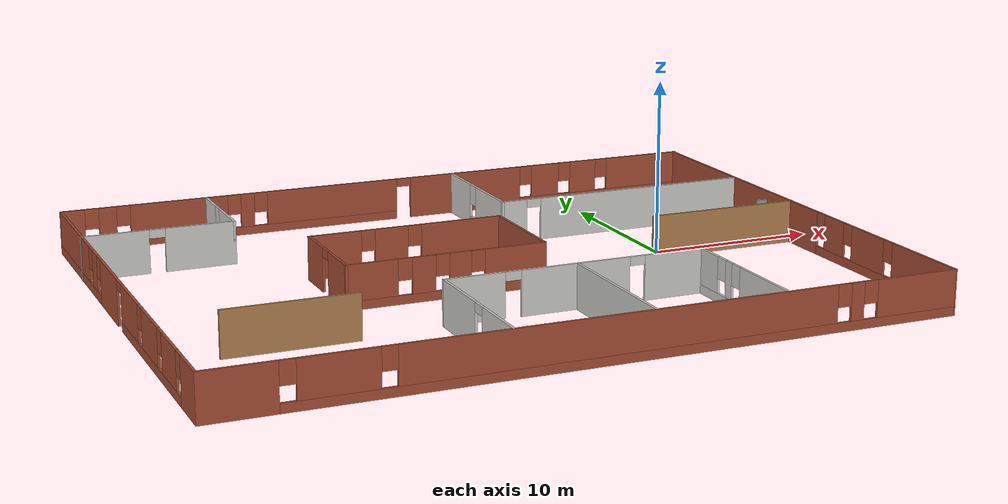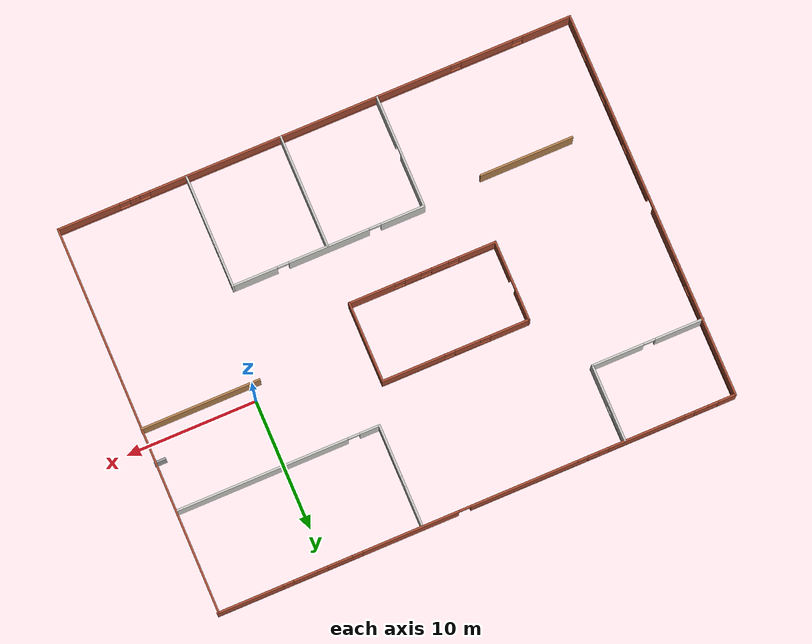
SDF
<?xml version='1.0'?>
<sdf version='1.6'>
  <model name='Office2'>
    <pose frame=''>-11.6266 -1.74216 0 0 -0 0</pose>
    <link name='Door_3'>
      <collision name='Door_3_Collision'>
        <geometry>
          <box>
            <size>0.9 0.17 2</size>
          </box>
        </geometry>
        <pose frame=''>0 0 1 0 -0 0</pose>
      </collision>
      <visual name='Door_3_Visual'>
        <pose frame=''>0 0 1 0 -0 0</pose>
        <geometry>
          <box>
            <size>0.9 0.17 2</size>
          </box>
        </geometry>
        <material>
          <script>
            <uri>file://media/materials/scripts/gazebo.material</uri>
            <name>Gazebo/Grey</name>
          </script>
        </material>
      </visual>
      <pose frame=''>19.6108 3.24042 0 0 -0 0</pose>
    </link>
    <link name='Wall_0'>
      <pose frame=''>-19.9784 0.000161 0 0 -0 1.5708</pose>
      <visual name='Wall_0_Visual_0'>
        <pose frame=''>-13.757 0 1.25 0 -0 0</pose>
        <geometry>
          <box>
            <size>2.48598 0.15 2.5</size>
          </box>
        </geometry>
        <material>
          <script>
            <uri>file://media/materials/scripts/gazebo.material</uri>
            <name>Gazebo/Bricks</name>
          </script>
          <ambient>1 1 1 1</ambient>
        </material>
        <meta>
          <layer>0</layer>
        </meta>
      </visual>
      <collision name='Wall_0_Collision_0'>
        <geometry>
          <box>
            <size>2.48598 0.15 2.5</size>
          </box>
        </geometry>
        <pose frame=''>-13.757 0 1.25 0 -0 0</pose>
      </collision>
      <visual name='Wall_0_Visual_1'>
        <pose frame=''>2.2039 0 1.25 0 -0 0</pose>
        <geometry>
          <box>
            <size>3.96148 0.15 2.5</size>
          </box>
        </geometry>
        <material>
          <script>
            <uri>file://media/materials/scripts/gazebo.material</uri>
            <name>Gazebo/Bricks</name>
          </script>
          <ambient>1 1 1 1</ambient>
        </material>
        <meta>
          <layer>0</layer>
        </meta>
      </visual>
      <collision name='Wall_0_Collision_1'>
        <geometry>
          <box>
            <size>3.96148 0.15 2.5</size>
          </box>
        </geometry>
        <pose frame=''>2.2039 0 1.25 0 -0 0</pose>
      </collision>
      <visual name='Wall_0_Visual_2'>
        <pose frame=''>-6.59543 0 0.25 0 -0 0</pose>
        <geometry>
          <box>
            <size>11.8372 0.15 0.5</size>
          </box>
        </geometry>
        <material>
          <script>
            <uri>file://media/materials/scripts/gazebo.material</uri>
            <name>Gazebo/Bricks</name>
          </script>
          <ambient>1 1 1 1</ambient>
        </material>
        <meta>
          <layer>0</layer>
        </meta>
      </visual>
      <collision name='Wall_0_Collision_2'>
        <geometry>
          <box>
            <size>11.8372 0.15 0.5</size>
          </box>
        </geometry>
        <pose frame=''>-6.59543 0 0.25 0 -0 0</pose>
      </collision>
      <visual name='Wall_0_Visual_3'>
        <pose frame=''>9.59232 0 0.25 0 -0 0</pose>
        <geometry>
          <box>
            <size>10.8154 0.15 0.5</size>
          </box>
        </geometry>
        <material>
          <script>
            <uri>file://media/materials/scripts/gazebo.material</uri>
            <name>Gazebo/Bricks</name>
          </script>
          <ambient>1 1 1 1</ambient>
        </material>
        <meta>
          <layer>0</layer>
        </meta>
      </visual>
      <collision name='Wall_0_Collision_3'>
        <geometry>
          <box>
            <size>10.8154 0.15 0.5</size>
          </box>
        </geometry>
        <pose frame=''>9.59232 0 0.25 0 -0 0</pose>
      </collision>
      <visual name='Wall_0_Visual_4'>
        <pose frame=''>-10.3805 0 1.5 0 -0 0</pose>
        <geometry>
          <box>
            <size>2.6671 0.15 2</size>
          </box>
        </geometry>
        <material>
          <script>
            <uri>file://media/materials/scripts/gazebo.material</uri>
            <name>Gazebo/Bricks</name>
          </script>
          <ambient>1 1 1 1</ambient>
        </material>
        <meta>
          <layer>0</layer>
        </meta>
      </visual>
      <collision name='Wall_0_Collision_4'>
        <geometry>
          <box>
            <size>2.6671 0.15 2</size>
          </box>
        </geometry>
        <pose frame=''>-10.3805 0 1.5 0 -0 0</pose>
      </collision>
      <visual name='Wall_0_Visual_5'>
        <pose frame=''>-6.66573 0 1.5 0 -0 0</pose>
        <geometry>
          <box>
            <size>3.1624 0.15 2</size>
          </box>
        </geometry>
        <material>
          <script>
            <uri>file://media/materials/scripts/gazebo.material</uri>
            <name>Gazebo/Bricks</name>
          </script>
          <ambient>1 1 1 1</ambient>
        </material>
        <meta>
          <layer>0</layer>
        </meta>
      </visual>
      <collision name='Wall_0_Collision_5'>
        <geometry>
          <box>
            <size>3.1624 0.15 2</size>
          </box>
        </geometry>
        <pose frame=''>-6.66573 0 1.5 0 -0 0</pose>
      </collision>
      <visual name='Wall_0_Visual_6'>
        <pose frame=''>-2.48068 0 1.5 0 -0 0</pose>
        <geometry>
          <box>
            <size>3.6077 0.15 2</size>
          </box>
        </geometry>
        <material>
          <script>
            <uri>file://media/materials/scripts/gazebo.material</uri>
            <name>Gazebo/Bricks</name>
          </script>
          <ambient>1 1 1 1</ambient>
        </material>
        <meta>
          <layer>0</layer>
        </meta>
      </visual>
      <collision name='Wall_0_Collision_6'>
        <geometry>
          <box>
            <size>3.6077 0.15 2</size>
          </box>
        </geometry>
        <pose frame=''>-2.48068 0 1.5 0 -0 0</pose>
      </collision>
      <visual name='Wall_0_Visual_7'>
        <pose frame=''>-2.48068 0 1.5 0 -0 0</pose>
        <geometry>
          <box>
            <size>3.6077 0.15 2</size>
          </box>
        </geometry>
        <material>
          <script>
            <uri>file://media/materials/scripts/gazebo.material</uri>
            <name>Gazebo/Bricks</name>
          </script>
          <ambient>1 1 1 1</ambient>
        </material>
        <meta>
          <layer>0</layer>
        </meta>
      </visual>
      <collision name='Wall_0_Collision_7'>
        <geometry>
          <box>
            <size>3.6077 0.15 2</size>
          </box>
        </geometry>
        <pose frame=''>-2.48068 0 1.5 0 -0 0</pose>
      </collision>
      <visual name='Wall_0_Visual_8'>
        <pose frame=''>5.57524 0 1.5 0 -0 0</pose>
        <geometry>
          <box>
            <size>1.1812 0.15 2</size>
          </box>
        </geometry>
        <material>
          <script>
            <uri>file://media/materials/scripts/gazebo.material</uri>
            <name>Gazebo/Bricks</name>
          </script>
          <ambient>1 1 1 1</ambient>
        </material>
        <meta>
          <layer>0</layer>
        </meta>
      </visual>
      <collision name='Wall_0_Collision_8'>
        <geometry>
          <box>
            <size>1.1812 0.15 2</size>
          </box>
        </geometry>
        <pose frame=''>5.57524 0 1.5 0 -0 0</pose>
      </collision>
      <visual name='Wall_0_Visual_9'>
        <pose frame=''>10.9829 0 1.5 0 -0 0</pose>
        <geometry>
          <box>
            <size>8.03416 0.15 2</size>
          </box>
        </geometry>
        <material>
          <script>
            <uri>file://media/materials/scripts/gazebo.material</uri>
            <name>Gazebo/Bricks</name>
          </script>
          <ambient>1 1 1 1</ambient>
        </material>
        <meta>
          <layer>0</layer>
        </meta>
      </visual>
      <collision name='Wall_0_Collision_9'>
        <geometry>
          <box>
            <size>8.03416 0.15 2</size>
          </box>
        </geometry>
        <pose frame=''>10.9829 0 1.5 0 -0 0</pose>
      </collision>
      <visual name='Wall_0_Visual_10'>
        <pose frame=''>-12.114 0 1.9 0 -0 0</pose>
        <geometry>
          <box>
            <size>0.8 0.15 1.2</size>
          </box>
        </geometry>
        <material>
          <script>
            <uri>file://media/materials/scripts/gazebo.material</uri>
            <name>Gazebo/Bricks</name>
          </script>
          <ambient>1 1 1 1</ambient>
        </material>
        <meta>
          <layer>0</layer>
        </meta>
      </visual>
      <collision name='Wall_0_Collision_10'>
        <geometry>
          <box>
            <size>0.8 0.15 1.2</size>
          </box>
        </geometry>
        <pose frame=''>-12.114 0 1.9 0 -0 0</pose>
      </collision>
      <visual name='Wall_0_Visual_11'>
        <pose frame=''>4.58464 0 1.9 0 -0 0</pose>
        <geometry>
          <box>
            <size>0.8 0.15 1.2</size>
          </box>
        </geometry>
        <material>
          <script>
            <uri>file://media/materials/scripts/gazebo.material</uri>
            <name>Gazebo/Bricks</name>
          </script>
          <ambient>1 1 1 1</ambient>
        </material>
        <meta>
          <layer>0</layer>
        </meta>
      </visual>
      <collision name='Wall_0_Collision_11'>
        <geometry>
          <box>
            <size>0.8 0.15 1.2</size>
          </box>
        </geometry>
        <pose frame=''>4.58464 0 1.9 0 -0 0</pose>
      </collision>
      <visual name='Wall_0_Visual_12'>
        <pose frame=''>-8.64693 0 1.9 0 -0 0</pose>
        <geometry>
          <box>
            <size>0.8 0.15 1.2</size>
          </box>
        </geometry>
        <material>
          <script>
            <uri>file://media/materials/scripts/gazebo.material</uri>
            <name>Gazebo/Bricks</name>
          </script>
          <ambient>1 1 1 1</ambient>
        </material>
        <meta>
          <layer>0</layer>
        </meta>
      </visual>
      <collision name='Wall_0_Collision_12'>
        <geometry>
          <box>
            <size>0.8 0.15 1.2</size>
          </box>
        </geometry>
        <pose frame=''>-8.64693 0 1.9 0 -0 0</pose>
      </collision>
      <visual name='Wall_0_Visual_13'>
        <pose frame=''>-4.68453 0 1.9 0 -0 0</pose>
        <geometry>
          <box>
            <size>0.8 0.15 1.2</size>
          </box>
        </geometry>
        <material>
          <script>
            <uri>file://media/materials/scripts/gazebo.material</uri>
            <name>Gazebo/Bricks</name>
          </script>
          <ambient>1 1 1 1</ambient>
        </material>
        <meta>
          <layer>0</layer>
        </meta>
      </visual>
      <collision name='Wall_0_Collision_13'>
        <geometry>
          <box>
            <size>0.8 0.15 1.2</size>
          </box>
        </geometry>
        <pose frame=''>-4.68453 0 1.9 0 -0 0</pose>
      </collision>
      <visual name='Wall_0_Visual_14'>
        <pose frame=''>6.56584 0 1.9 0 -0 0</pose>
        <geometry>
          <box>
            <size>0.8 0.15 1.2</size>
          </box>
        </geometry>
        <material>
          <script>
            <uri>file://media/materials/scripts/gazebo.material</uri>
            <name>Gazebo/Bricks</name>
          </script>
          <ambient>1 1 1 1</ambient>
        </material>
        <meta>
          <layer>0</layer>
        </meta>
      </visual>
      <collision name='Wall_0_Collision_14'>
        <geometry>
          <box>
            <size>0.8 0.15 1.2</size>
          </box>
        </geometry>
        <pose frame=''>6.56584 0 1.9 0 -0 0</pose>
      </collision>
      <visual name='Wall_0_Visual_15'>
        <pose frame=''>-0.226838 0 2.25 0 -0 0</pose>
        <geometry>
          <box>
            <size>0.9 0.15 0.5</size>
          </box>
        </geometry>
        <material>
          <script>
            <uri>file://media/materials/scripts/gazebo.material</uri>
            <name>Gazebo/Bricks</name>
          </script>
          <ambient>1 1 1 1</ambient>
        </material>
        <meta>
          <layer>0</layer>
        </meta>
      </visual>
      <collision name='Wall_0_Collision_15'>
        <geometry>
          <box>
            <size>0.9 0.15 0.5</size>
          </box>
        </geometry>
        <pose frame=''>-0.226838 0 2.25 0 -0 0</pose>
      </collision>
      <visual name='Wall_0_Visual_16'>
        <pose frame=''>-0.226838 0 2.25 0 -0 0</pose>
        <geometry>
          <box>
            <size>0.9 0.15 0.5</size>
          </box>
        </geometry>
        <material>
          <script>
            <uri>file://media/materials/scripts/gazebo.material</uri>
            <name>Gazebo/Bricks</name>
          </script>
          <ambient>1 1 1 1</ambient>
        </material>
        <meta>
          <layer>0</layer>
        </meta>
      </visual>
      <collision name='Wall_0_Collision_16'>
        <geometry>
          <box>
            <size>0.9 0.15 0.5</size>
          </box>
        </geometry>
        <pose frame=''>-0.226838 0 2.25 0 -0 0</pose>
      </collision>
    </link>
    <link name='Wall_11'>
      <pose frame=''>-15.7131 9.0425 0 0 -0 0</pose>
      <visual name='Wall_11_Visual_0'>
        <pose frame=''>-2.47517 0 1.25 0 -0 0</pose>
        <geometry>
          <box>
            <size>3.79967 0.15 2.5</size>
          </box>
        </geometry>
        <material>
          <script>
            <uri>file://media/materials/scripts/gazebo.material</uri>
            <name>Gazebo/CeilingTiled</name>
          </script>
          <ambient>0.203922 0.396078 0.643137 1</ambient>
        </material>
        <meta>
          <layer>0</layer>
        </meta>
      </visual>
      <collision name='Wall_11_Collision_0'>
        <geometry>
          <box>
            <size>3.79967 0.15 2.5</size>
          </box>
        </geometry>
        <pose frame=''>-2.47517 0 1.25 0 -0 0</pose>
      </collision>
      <visual name='Wall_11_Visual_1'>
        <pose frame=''>2.34983 0 1.25 0 -0 0</pose>
        <geometry>
          <box>
            <size>4.05033 0.15 2.5</size>
          </box>
        </geometry>
        <material>
          <script>
            <uri>file://media/materials/scripts/gazebo.material</uri>
            <name>Gazebo/CeilingTiled</name>
          </script>
          <ambient>0.203922 0.396078 0.643137 1</ambient>
        </material>
        <meta>
          <layer>0</layer>
        </meta>
      </visual>
      <collision name='Wall_11_Collision_1'>
        <geometry>
          <box>
            <size>4.05033 0.15 2.5</size>
          </box>
        </geometry>
        <pose frame=''>2.34983 0 1.25 0 -0 0</pose>
      </collision>
      <visual name='Wall_11_Visual_2'>
        <pose frame=''>-0.125334 0 2.25 0 -0 0</pose>
        <geometry>
          <box>
            <size>0.9 0.15 0.5</size>
          </box>
        </geometry>
        <material>
          <script>
            <uri>file://media/materials/scripts/gazebo.material</uri>
            <name>Gazebo/CeilingTiled</name>
          </script>
          <ambient>0.203922 0.396078 0.643137 1</ambient>
        </material>
        <meta>
          <layer>0</layer>
        </meta>
      </visual>
      <collision name='Wall_11_Collision_2'>
        <geometry>
          <box>
            <size>0.9 0.15 0.5</size>
          </box>
        </geometry>
        <pose frame=''>-0.125334 0 2.25 0 -0 0</pose>
      </collision>
    </link>
    <link name='Wall_15'>
      <pose frame=''>-11.4131 11.9675 0 0 -0 1.5708</pose>
      <visual name='Wall_15_Visual_0'>
        <pose frame=''>-1.49971 0 1.25 0 -0 0</pose>
        <geometry>
          <box>
            <size>3.00058 0.15 2.5</size>
          </box>
        </geometry>
        <material>
          <script>
            <uri>file://media/materials/scripts/gazebo.material</uri>
            <name>Gazebo/CeilingTiled</name>
          </script>
          <ambient>1 1 1 1</ambient>
        </material>
        <meta>
          <layer>0</layer>
        </meta>
      </visual>
      <collision name='Wall_15_Collision_0'>
        <geometry>
          <box>
            <size>3.00058 0.15 2.5</size>
          </box>
        </geometry>
        <pose frame=''>-1.49971 0 1.25 0 -0 0</pose>
      </collision>
      <visual name='Wall_15_Visual_1'>
        <pose frame=''>1.50029 0 0.25 0 -0 0</pose>
        <geometry>
          <box>
            <size>2.99942 0.15 0.5</size>
          </box>
        </geometry>
        <material>
          <script>
            <uri>file://media/materials/scripts/gazebo.material</uri>
            <name>Gazebo/CeilingTiled</name>
          </script>
          <ambient>1 1 1 1</ambient>
        </material>
        <meta>
          <layer>0</layer>
        </meta>
      </visual>
      <collision name='Wall_15_Collision_1'>
        <geometry>
          <box>
            <size>2.99942 0.15 0.5</size>
          </box>
        </geometry>
        <pose frame=''>1.50029 0 0.25 0 -0 0</pose>
      </collision>
      <visual name='Wall_15_Visual_2'>
        <pose frame=''>1.90029 0 1.5 0 -0 0</pose>
        <geometry>
          <box>
            <size>2.19942 0.15 2</size>
          </box>
        </geometry>
        <material>
          <script>
            <uri>file://media/materials/scripts/gazebo.material</uri>
            <name>Gazebo/CeilingTiled</name>
          </script>
          <ambient>1 1 1 1</ambient>
        </material>
        <meta>
          <layer>0</layer>
        </meta>
      </visual>
      <collision name='Wall_15_Collision_2'>
        <geometry>
          <box>
            <size>2.19942 0.15 2</size>
          </box>
        </geometry>
        <pose frame=''>1.90029 0 1.5 0 -0 0</pose>
      </collision>
      <visual name='Wall_15_Visual_3'>
        <pose frame=''>0.400581 0 1.9 0 -0 0</pose>
        <geometry>
          <box>
            <size>0.8 0.15 1.2</size>
          </box>
        </geometry>
        <material>
          <script>
            <uri>file://media/materials/scripts/gazebo.material</uri>
            <name>Gazebo/CeilingTiled</name>
          </script>
          <ambient>1 1 1 1</ambient>
        </material>
        <meta>
          <layer>0</layer>
        </meta>
      </visual>
      <collision name='Wall_15_Collision_3'>
        <geometry>
          <box>
            <size>0.8 0.15 1.2</size>
          </box>
        </geometry>
        <pose frame=''>0.400581 0 1.9 0 -0 0</pose>
      </collision>
    </link>
    <link name='Wall_17'>
      <pose frame=''>4.25654 10.9903 0 0 -0 -1.5708</pose>
      <visual name='Wall_17_Visual_0'>
        <pose frame=''>-2.42895 0 1.25 0 -0 0</pose>
        <geometry>
          <box>
            <size>3.1421 0.15 2.5</size>
          </box>
        </geometry>
        <material>
          <script>
            <uri>file://media/materials/scripts/gazebo.material</uri>
            <name>Gazebo/CeilingTiled</name>
          </script>
          <ambient>1 1 1 1</ambient>
        </material>
        <meta>
          <layer>0</layer>
        </meta>
      </visual>
      <collision name='Wall_17_Collision_0'>
        <geometry>
          <box>
            <size>3.1421 0.15 2.5</size>
          </box>
        </geometry>
        <pose frame=''>-2.42895 0 1.25 0 -0 0</pose>
      </collision>
      <visual name='Wall_17_Visual_1'>
        <pose frame=''>1.57105 0 0.25 0 -0 0</pose>
        <geometry>
          <box>
            <size>4.8579 0.15 0.5</size>
          </box>
        </geometry>
        <material>
          <script>
            <uri>file://media/materials/scripts/gazebo.material</uri>
            <name>Gazebo/CeilingTiled</name>
          </script>
          <ambient>1 1 1 1</ambient>
        </material>
        <meta>
          <layer>0</layer>
        </meta>
      </visual>
      <collision name='Wall_17_Collision_1'>
        <geometry>
          <box>
            <size>4.8579 0.15 0.5</size>
          </box>
        </geometry>
        <pose frame=''>1.57105 0 0.25 0 -0 0</pose>
      </collision>
      <visual name='Wall_17_Visual_2'>
        <pose frame=''>1.97105 0 1.5 0 -0 0</pose>
        <geometry>
          <box>
            <size>4.0579 0.15 2</size>
          </box>
        </geometry>
        <material>
          <script>
            <uri>file://media/materials/scripts/gazebo.material</uri>
            <name>Gazebo/CeilingTiled</name>
          </script>
          <ambient>1 1 1 1</ambient>
        </material>
        <meta>
          <layer>0</layer>
        </meta>
      </visual>
      <collision name='Wall_17_Collision_2'>
        <geometry>
          <box>
            <size>4.0579 0.15 2</size>
          </box>
        </geometry>
        <pose frame=''>1.97105 0 1.5 0 -0 0</pose>
      </collision>
      <visual name='Wall_17_Visual_3'>
        <pose frame=''>-0.457904 0 1.9 0 -0 0</pose>
        <geometry>
          <box>
            <size>0.8 0.15 1.2</size>
          </box>
        </geometry>
        <material>
          <script>
            <uri>file://media/materials/scripts/gazebo.material</uri>
            <name>Gazebo/CeilingTiled</name>
          </script>
          <ambient>1 1 1 1</ambient>
        </material>
        <meta>
          <layer>0</layer>
        </meta>
      </visual>
      <collision name='Wall_17_Collision_3'>
        <geometry>
          <box>
            <size>0.8 0.15 1.2</size>
          </box>
        </geometry>
        <pose frame=''>-0.457904 0 1.9 0 -0 0</pose>
      </collision>
    </link>
    <link name='Wall_18'>
      <pose frame=''>12.0565 7.06533 0 0 -0 0</pose>
      <visual name='Wall_18_Visual_0'>
        <pose frame=''>-7.0719 0 1.25 0 -0 0</pose>
        <geometry>
          <box>
            <size>1.6062 0.15 2.5</size>
          </box>
        </geometry>
        <material>
          <script>
            <uri>file://media/materials/scripts/gazebo.material</uri>
            <name>Gazebo/CeilingTiled</name>
          </script>
          <ambient>0.203922 0.396078 0.643137 1</ambient>
        </material>
        <meta>
          <layer>0</layer>
        </meta>
      </visual>
      <collision name='Wall_18_Collision_0'>
        <geometry>
          <box>
            <size>1.6062 0.15 2.5</size>
          </box>
        </geometry>
        <pose frame=''>-7.0719 0 1.25 0 -0 0</pose>
      </collision>
      <visual name='Wall_18_Visual_1'>
        <pose frame=''>1.2531 0 1.25 0 -0 0</pose>
        <geometry>
          <box>
            <size>13.2438 0.15 2.5</size>
          </box>
        </geometry>
        <material>
          <script>
            <uri>file://media/materials/scripts/gazebo.material</uri>
            <name>Gazebo/CeilingTiled</name>
          </script>
          <ambient>0.203922 0.396078 0.643137 1</ambient>
        </material>
        <meta>
          <layer>0</layer>
        </meta>
      </visual>
      <collision name='Wall_18_Collision_1'>
        <geometry>
          <box>
            <size>13.2438 0.15 2.5</size>
          </box>
        </geometry>
        <pose frame=''>1.2531 0 1.25 0 -0 0</pose>
      </collision>
      <visual name='Wall_18_Visual_2'>
        <pose frame=''>-5.8188 0 2.25 0 -0 0</pose>
        <geometry>
          <box>
            <size>0.9 0.15 0.5</size>
          </box>
        </geometry>
        <material>
          <script>
            <uri>file://media/materials/scripts/gazebo.material</uri>
            <name>Gazebo/CeilingTiled</name>
          </script>
          <ambient>0.203922 0.396078 0.643137 1</ambient>
        </material>
        <meta>
          <layer>0</layer>
        </meta>
      </visual>
      <collision name='Wall_18_Collision_2'>
        <geometry>
          <box>
            <size>0.9 0.15 0.5</size>
          </box>
        </geometry>
        <pose frame=''>-5.8188 0 2.25 0 -0 0</pose>
      </collision>
    </link>
    <link name='Wall_20'>
      <pose frame=''>9.98786 -10.5734 0 0 -0 1.5708</pose>
      <visual name='Wall_20_Visual_0'>
        <pose frame=''>-2.061 0 1.25 0 -0 0</pose>
        <geometry>
          <box>
            <size>4.62799 0.15 2.5</size>
          </box>
        </geometry>
        <material>
          <script>
            <uri>file://media/materials/scripts/gazebo.material</uri>
            <name>Gazebo/CeilingTiled</name>
          </script>
          <ambient>1 1 1 1</ambient>
        </material>
        <meta>
          <layer>0</layer>
        </meta>
      </visual>
      <collision name='Wall_20_Collision_0'>
        <geometry>
          <box>
            <size>4.62799 0.15 2.5</size>
          </box>
        </geometry>
        <pose frame=''>-2.061 0 1.25 0 -0 0</pose>
      </collision>
      <visual name='Wall_20_Visual_1'>
        <pose frame=''>2.314 0 0.25 0 -0 0</pose>
        <geometry>
          <box>
            <size>4.12201 0.15 0.5</size>
          </box>
        </geometry>
        <material>
          <script>
            <uri>file://media/materials/scripts/gazebo.material</uri>
            <name>Gazebo/CeilingTiled</name>
          </script>
          <ambient>1 1 1 1</ambient>
        </material>
        <meta>
          <layer>0</layer>
        </meta>
      </visual>
      <collision name='Wall_20_Collision_1'>
        <geometry>
          <box>
            <size>4.12201 0.15 0.5</size>
          </box>
        </geometry>
        <pose frame=''>2.314 0 0.25 0 -0 0</pose>
      </collision>
      <visual name='Wall_20_Visual_2'>
        <pose frame=''>1.36057 0 1.5 0 -0 0</pose>
        <geometry>
          <box>
            <size>0.615141 0.15 2</size>
          </box>
        </geometry>
        <material>
          <script>
            <uri>file://media/materials/scripts/gazebo.material</uri>
            <name>Gazebo/CeilingTiled</name>
          </script>
          <ambient>1 1 1 1</ambient>
        </material>
        <meta>
          <layer>0</layer>
        </meta>
      </visual>
      <collision name='Wall_20_Collision_2'>
        <geometry>
          <box>
            <size>0.615141 0.15 2</size>
          </box>
        </geometry>
        <pose frame=''>1.36057 0 1.5 0 -0 0</pose>
      </collision>
      <visual name='Wall_20_Visual_3'>
        <pose frame=''>3.42157 0 1.5 0 -0 0</pose>
        <geometry>
          <box>
            <size>1.90687 0.15 2</size>
          </box>
        </geometry>
        <material>
          <script>
            <uri>file://media/materials/scripts/gazebo.material</uri>
            <name>Gazebo/CeilingTiled</name>
          </script>
          <ambient>1 1 1 1</ambient>
        </material>
        <meta>
          <layer>0</layer>
        </meta>
      </visual>
      <collision name='Wall_20_Collision_3'>
        <geometry>
          <box>
            <size>1.90687 0.15 2</size>
          </box>
        </geometry>
        <pose frame=''>3.42157 0 1.5 0 -0 0</pose>
      </collision>
      <visual name='Wall_20_Visual_4'>
        <pose frame=''>0.652994 0 1.9 0 -0 0</pose>
        <geometry>
          <box>
            <size>0.8 0.15 1.2</size>
          </box>
        </geometry>
        <material>
          <script>
            <uri>file://media/materials/scripts/gazebo.material</uri>
            <name>Gazebo/CeilingTiled</name>
          </script>
          <ambient>1 1 1 1</ambient>
        </material>
        <meta>
          <layer>0</layer>
        </meta>
      </visual>
      <collision name='Wall_20_Collision_4'>
        <geometry>
          <box>
            <size>0.8 0.15 1.2</size>
          </box>
        </geometry>
        <pose frame=''>0.652994 0 1.9 0 -0 0</pose>
      </collision>
      <visual name='Wall_20_Visual_5'>
        <pose frame=''>2.06813 0 1.9 0 -0 0</pose>
        <geometry>
          <box>
            <size>0.8 0.15 1.2</size>
          </box>
        </geometry>
        <material>
          <script>
            <uri>file://media/materials/scripts/gazebo.material</uri>
            <name>Gazebo/CeilingTiled</name>
          </script>
          <ambient>1 1 1 1</ambient>
        </material>
        <meta>
          <layer>0</layer>
        </meta>
      </visual>
      <collision name='Wall_20_Collision_5'>
        <geometry>
          <box>
            <size>0.8 0.15 1.2</size>
          </box>
        </geometry>
        <pose frame=''>2.06813 0 1.9 0 -0 0</pose>
      </collision>
    </link>
    <link name='Wall_21'>
      <pose frame=''>2.56286 -6.27339 0 0 -0 3.14159</pose>
      <visual name='Wall_21_Visual_0'>
        <pose frame=''>-5.74168 0 1.25 0 -0 0</pose>
        <geometry>
          <box>
            <size>3.51664 0.15 2.5</size>
          </box>
        </geometry>
        <material>
          <script>
            <uri>file://media/materials/scripts/gazebo.material</uri>
            <name>Gazebo/CeilingTiled</name>
          </script>
          <ambient>0.203922 0.396078 0.643137 1</ambient>
        </material>
        <meta>
          <layer>0</layer>
        </meta>
      </visual>
      <collision name='Wall_21_Collision_0'>
        <geometry>
          <box>
            <size>3.51664 0.15 2.5</size>
          </box>
        </geometry>
        <pose frame=''>-5.74168 0 1.25 0 -0 0</pose>
      </collision>
      <visual name='Wall_21_Visual_1'>
        <pose frame=''>0.03987 0 1.25 0 -0 0</pose>
        <geometry>
          <box>
            <size>6.24646 0.15 2.5</size>
          </box>
        </geometry>
        <material>
          <script>
            <uri>file://media/materials/scripts/gazebo.material</uri>
            <name>Gazebo/CeilingTiled</name>
          </script>
          <ambient>0.203922 0.396078 0.643137 1</ambient>
        </material>
        <meta>
          <layer>0</layer>
        </meta>
      </visual>
      <collision name='Wall_21_Collision_1'>
        <geometry>
          <box>
            <size>6.24646 0.15 2.5</size>
          </box>
        </geometry>
        <pose frame=''>0.03987 0 1.25 0 -0 0</pose>
      </collision>
      <visual name='Wall_21_Visual_2'>
        <pose frame=''>5.78155 0 1.25 0 -0 0</pose>
        <geometry>
          <box>
            <size>3.4369 0.15 2.5</size>
          </box>
        </geometry>
        <material>
          <script>
            <uri>file://media/materials/scripts/gazebo.material</uri>
            <name>Gazebo/CeilingTiled</name>
          </script>
          <ambient>0.203922 0.396078 0.643137 1</ambient>
        </material>
        <meta>
          <layer>0</layer>
        </meta>
      </visual>
      <collision name='Wall_21_Collision_2'>
        <geometry>
          <box>
            <size>3.4369 0.15 2.5</size>
          </box>
        </geometry>
        <pose frame=''>5.78155 0 1.25 0 -0 0</pose>
      </collision>
      <visual name='Wall_21_Visual_3'>
        <pose frame=''>-3.53336 0 2.25 0 -0 0</pose>
        <geometry>
          <box>
            <size>0.9 0.15 0.5</size>
          </box>
        </geometry>
        <material>
          <script>
            <uri>file://media/materials/scripts/gazebo.material</uri>
            <name>Gazebo/CeilingTiled</name>
          </script>
          <ambient>0.203922 0.396078 0.643137 1</ambient>
        </material>
        <meta>
          <layer>0</layer>
        </meta>
      </visual>
      <collision name='Wall_21_Collision_3'>
        <geometry>
          <box>
            <size>0.9 0.15 0.5</size>
          </box>
        </geometry>
        <pose frame=''>-3.53336 0 2.25 0 -0 0</pose>
      </collision>
      <visual name='Wall_21_Visual_4'>
        <pose frame=''>3.6131 0 2.25 0 -0 0</pose>
        <geometry>
          <box>
            <size>0.9 0.15 0.5</size>
          </box>
        </geometry>
        <material>
          <script>
            <uri>file://media/materials/scripts/gazebo.material</uri>
            <name>Gazebo/CeilingTiled</name>
          </script>
          <ambient>0.203922 0.396078 0.643137 1</ambient>
        </material>
        <meta>
          <layer>0</layer>
        </meta>
      </visual>
      <collision name='Wall_21_Collision_4'>
        <geometry>
          <box>
            <size>0.9 0.15 0.5</size>
          </box>
        </geometry>
        <pose frame=''>3.6131 0 2.25 0 -0 0</pose>
      </collision>
    </link>
    <link name='Wall_22'>
      <pose frame=''>-4.86214 -10.5734 0 0 -0 -1.5708</pose>
      <visual name='Wall_22_Visual_0'>
        <pose frame=''>-2.27908 0 1.25 0 -0 0</pose>
        <geometry>
          <box>
            <size>4.19185 0.15 2.5</size>
          </box>
        </geometry>
        <material>
          <script>
            <uri>file://media/materials/scripts/gazebo.material</uri>
            <name>Gazebo/CeilingTiled</name>
          </script>
          <ambient>1 1 1 1</ambient>
        </material>
        <meta>
          <layer>0</layer>
        </meta>
      </visual>
      <collision name='Wall_22_Collision_0'>
        <geometry>
          <box>
            <size>4.19185 0.15 2.5</size>
          </box>
        </geometry>
        <pose frame=''>-2.27908 0 1.25 0 -0 0</pose>
      </collision>
      <visual name='Wall_22_Visual_1'>
        <pose frame=''>2.54592 0 1.25 0 -0 0</pose>
        <geometry>
          <box>
            <size>3.65815 0.15 2.5</size>
          </box>
        </geometry>
        <material>
          <script>
            <uri>file://media/materials/scripts/gazebo.material</uri>
            <name>Gazebo/CeilingTiled</name>
          </script>
          <ambient>1 1 1 1</ambient>
        </material>
        <meta>
          <layer>0</layer>
        </meta>
      </visual>
      <collision name='Wall_22_Collision_1'>
        <geometry>
          <box>
            <size>3.65815 0.15 2.5</size>
          </box>
        </geometry>
        <pose frame=''>2.54592 0 1.25 0 -0 0</pose>
      </collision>
      <visual name='Wall_22_Visual_2'>
        <pose frame=''>0.266848 0 2.25 0 -0 0</pose>
        <geometry>
          <box>
            <size>0.9 0.15 0.5</size>
          </box>
        </geometry>
        <material>
          <script>
            <uri>file://media/materials/scripts/gazebo.material</uri>
            <name>Gazebo/CeilingTiled</name>
          </script>
          <ambient>1 1 1 1</ambient>
        </material>
        <meta>
          <layer>0</layer>
        </meta>
      </visual>
      <collision name='Wall_22_Collision_2'>
        <geometry>
          <box>
            <size>0.9 0.15 0.5</size>
          </box>
        </geometry>
        <pose frame=''>0.266848 0 2.25 0 -0 0</pose>
      </collision>
    </link>
    <link name='Wall_24'>
      <collision name='Wall_24_Collision'>
        <geometry>
          <box>
            <size>8.75 0.15 2.5</size>
          </box>
        </geometry>
        <pose frame=''>0 0 1.25 0 -0 0</pose>
      </collision>
      <visual name='Wall_24_Visual'>
        <pose frame=''>0 0 1.25 0 -0 0</pose>
        <geometry>
          <box>
            <size>8.75 0.15 2.5</size>
          </box>
        </geometry>
        <material>
          <script>
            <uri>file://media/materials/scripts/gazebo.material</uri>
            <name>Gazebo/CeilingTiled</name>
          </script>
          <ambient>1 1 1 1</ambient>
        </material>
        <meta>
          <layer>0</layer>
        </meta>
      </visual>
      <pose frame=''>2.62913 -10.6118 0 0 -0 -1.5708</pose>
    </link>
    <link name='Wall_26'>
      <pose frame=''>-2.87549 4.23102 0 0 -0 0</pose>
      <visual name='Wall_26_Visual_0'>
        <pose frame=''>-4.21433 0 1.25 0 -0 0</pose>
        <geometry>
          <box>
            <size>3.07134 0.15 2.5</size>
          </box>
        </geometry>
        <material>
          <script>
            <uri>file://media/materials/scripts/gazebo.material</uri>
            <name>Gazebo/Bricks</name>
          </script>
          <ambient>1 1 1 1</ambient>
        </material>
        <meta>
          <layer>0</layer>
        </meta>
      </visual>
      <collision name='Wall_26_Collision_0'>
        <geometry>
          <box>
            <size>3.07134 0.15 2.5</size>
          </box>
        </geometry>
        <pose frame=''>-4.21433 0 1.25 0 -0 0</pose>
      </collision>
      <visual name='Wall_26_Visual_1'>
        <pose frame=''>1.53567 0 0.25 0 -0 0</pose>
        <geometry>
          <box>
            <size>8.42866 0.15 0.5</size>
          </box>
        </geometry>
        <material>
          <script>
            <uri>file://media/materials/scripts/gazebo.material</uri>
            <name>Gazebo/Bricks</name>
          </script>
          <ambient>1 1 1 1</ambient>
        </material>
        <meta>
          <layer>0</layer>
        </meta>
      </visual>
      <collision name='Wall_26_Collision_1'>
        <geometry>
          <box>
            <size>8.42866 0.15 0.5</size>
          </box>
        </geometry>
        <pose frame=''>1.53567 0 0.25 0 -0 0</pose>
      </collision>
      <visual name='Wall_26_Visual_2'>
        <pose frame=''>-0.898898 0 1.5 0 -0 0</pose>
        <geometry>
          <box>
            <size>1.95952 0.15 2</size>
          </box>
        </geometry>
        <material>
          <script>
            <uri>file://media/materials/scripts/gazebo.material</uri>
            <name>Gazebo/Bricks</name>
          </script>
          <ambient>1 1 1 1</ambient>
        </material>
        <meta>
          <layer>0</layer>
        </meta>
      </visual>
      <collision name='Wall_26_Collision_2'>
        <geometry>
          <box>
            <size>1.95952 0.15 2</size>
          </box>
        </geometry>
        <pose frame=''>-0.898898 0 1.5 0 -0 0</pose>
      </collision>
      <visual name='Wall_26_Visual_3'>
        <pose frame=''>3.31543 0 1.5 0 -0 0</pose>
        <geometry>
          <box>
            <size>4.86913 0.15 2</size>
          </box>
        </geometry>
        <material>
          <script>
            <uri>file://media/materials/scripts/gazebo.material</uri>
            <name>Gazebo/Bricks</name>
          </script>
          <ambient>1 1 1 1</ambient>
        </material>
        <meta>
          <layer>0</layer>
        </meta>
      </visual>
      <collision name='Wall_26_Collision_3'>
        <geometry>
          <box>
            <size>4.86913 0.15 2</size>
          </box>
        </geometry>
        <pose frame=''>3.31543 0 1.5 0 -0 0</pose>
      </collision>
      <visual name='Wall_26_Visual_4'>
        <pose frame=''>-2.27866 0 1.9 0 -0 0</pose>
        <geometry>
          <box>
            <size>0.8 0.15 1.2</size>
          </box>
        </geometry>
        <material>
          <script>
            <uri>file://media/materials/scripts/gazebo.material</uri>
            <name>Gazebo/Bricks</name>
          </script>
          <ambient>1 1 1 1</ambient>
        </material>
        <meta>
          <layer>0</layer>
        </meta>
      </visual>
      <collision name='Wall_26_Collision_4'>
        <geometry>
          <box>
            <size>0.8 0.15 1.2</size>
          </box>
        </geometry>
        <pose frame=''>-2.27866 0 1.9 0 -0 0</pose>
      </collision>
      <visual name='Wall_26_Visual_5'>
        <pose frame=''>0.480865 0 1.9 0 -0 0</pose>
        <geometry>
          <box>
            <size>0.8 0.15 1.2</size>
          </box>
        </geometry>
        <material>
          <script>
            <uri>file://media/materials/scripts/gazebo.material</uri>
            <name>Gazebo/Bricks</name>
          </script>
          <ambient>1 1 1 1</ambient>
        </material>
        <meta>
          <layer>0</layer>
        </meta>
      </visual>
      <collision name='Wall_26_Collision_5'>
        <geometry>
          <box>
            <size>0.8 0.15 1.2</size>
          </box>
        </geometry>
        <pose frame=''>0.480865 0 1.9 0 -0 0</pose>
      </collision>
    </link>
    <link name='Wall_27'>
      <collision name='Wall_27_Collision'>
        <geometry>
          <box>
            <size>6.25 0.15 2.5</size>
          </box>
        </geometry>
        <pose frame=''>0 0 1.25 0 -0 0</pose>
      </collision>
      <visual name='Wall_27_Visual'>
        <pose frame=''>0 0 1.25 0 -0 0</pose>
        <geometry>
          <box>
            <size>6.25 0.15 2.5</size>
          </box>
        </geometry>
        <material>
          <script>
            <uri>file://media/materials/scripts/gazebo.material</uri>
            <name>Gazebo/Bricks</name>
          </script>
          <ambient>1 1 1 1</ambient>
        </material>
        <meta>
          <layer>0</layer>
        </meta>
      </visual>
      <pose frame=''>2.79951 1.18102 0 0 -0 -1.5708</pose>
    </link>
    <link name='Wall_28'>
      <pose frame=''>-2.87549 -1.86898 0 0 -0 3.14159</pose>
      <visual name='Wall_28_Visual_0'>
        <pose frame=''>-3.95225 0 1.25 0 -0 0</pose>
        <geometry>
          <box>
            <size>3.59551 0.15 2.5</size>
          </box>
        </geometry>
        <material>
          <script>
            <uri>file://media/materials/scripts/gazebo.material</uri>
            <name>Gazebo/Bricks</name>
          </script>
          <ambient>1 1 1 1</ambient>
        </material>
        <meta>
          <layer>0</layer>
        </meta>
      </visual>
      <collision name='Wall_28_Collision_0'>
        <geometry>
          <box>
            <size>3.59551 0.15 2.5</size>
          </box>
        </geometry>
        <pose frame=''>-3.95225 0 1.25 0 -0 0</pose>
      </collision>
      <visual name='Wall_28_Visual_1'>
        <pose frame=''>1.79775 0 0.25 0 -0 0</pose>
        <geometry>
          <box>
            <size>7.90449 0.15 0.5</size>
          </box>
        </geometry>
        <material>
          <script>
            <uri>file://media/materials/scripts/gazebo.material</uri>
            <name>Gazebo/Bricks</name>
          </script>
          <ambient>1 1 1 1</ambient>
        </material>
        <meta>
          <layer>0</layer>
        </meta>
      </visual>
      <collision name='Wall_28_Collision_1'>
        <geometry>
          <box>
            <size>7.90449 0.15 0.5</size>
          </box>
        </geometry>
        <pose frame=''>1.79775 0 0.25 0 -0 0</pose>
      </collision>
      <visual name='Wall_28_Visual_2'>
        <pose frame=''>-0.728514 0 1.5 0 -0 0</pose>
        <geometry>
          <box>
            <size>1.25195 0.15 2</size>
          </box>
        </geometry>
        <material>
          <script>
            <uri>file://media/materials/scripts/gazebo.material</uri>
            <name>Gazebo/Bricks</name>
          </script>
          <ambient>1 1 1 1</ambient>
        </material>
        <meta>
          <layer>0</layer>
        </meta>
      </visual>
      <collision name='Wall_28_Collision_2'>
        <geometry>
          <box>
            <size>1.25195 0.15 2</size>
          </box>
        </geometry>
        <pose frame=''>-0.728514 0 1.5 0 -0 0</pose>
      </collision>
      <visual name='Wall_28_Visual_3'>
        <pose frame=''>1.35882 0 1.5 0 -0 0</pose>
        <geometry>
          <box>
            <size>1.32271 0.15 2</size>
          </box>
        </geometry>
        <material>
          <script>
            <uri>file://media/materials/scripts/gazebo.material</uri>
            <name>Gazebo/Bricks</name>
          </script>
          <ambient>1 1 1 1</ambient>
        </material>
        <meta>
          <layer>0</layer>
        </meta>
      </visual>
      <collision name='Wall_28_Collision_3'>
        <geometry>
          <box>
            <size>1.32271 0.15 2</size>
          </box>
        </geometry>
        <pose frame=''>1.35882 0 1.5 0 -0 0</pose>
      </collision>
      <visual name='Wall_28_Visual_4'>
        <pose frame=''>4.28509 0 1.5 0 -0 0</pose>
        <geometry>
          <box>
            <size>2.92983 0.15 2</size>
          </box>
        </geometry>
        <material>
          <script>
            <uri>file://media/materials/scripts/gazebo.material</uri>
            <name>Gazebo/Bricks</name>
          </script>
          <ambient>1 1 1 1</ambient>
        </material>
        <meta>
          <layer>0</layer>
        </meta>
      </visual>
      <collision name='Wall_28_Collision_4'>
        <geometry>
          <box>
            <size>2.92983 0.15 2</size>
          </box>
        </geometry>
        <pose frame=''>4.28509 0 1.5 0 -0 0</pose>
      </collision>
      <visual name='Wall_28_Visual_5'>
        <pose frame=''>-1.75449 0 1.9 0 -0 0</pose>
        <geometry>
          <box>
            <size>0.8 0.15 1.2</size>
          </box>
        </geometry>
        <material>
          <script>
            <uri>file://media/materials/scripts/gazebo.material</uri>
            <name>Gazebo/Bricks</name>
          </script>
          <ambient>1 1 1 1</ambient>
        </material>
        <meta>
          <layer>0</layer>
        </meta>
      </visual>
      <collision name='Wall_28_Collision_5'>
        <geometry>
          <box>
            <size>0.8 0.15 1.2</size>
          </box>
        </geometry>
        <pose frame=''>-1.75449 0 1.9 0 -0 0</pose>
      </collision>
      <visual name='Wall_28_Visual_6'>
        <pose frame=''>0.297463 0 1.9 0 -0 0</pose>
        <geometry>
          <box>
            <size>0.8 0.15 1.2</size>
          </box>
        </geometry>
        <material>
          <script>
            <uri>file://media/materials/scripts/gazebo.material</uri>
            <name>Gazebo/Bricks</name>
          </script>
          <ambient>1 1 1 1</ambient>
        </material>
        <meta>
          <layer>0</layer>
        </meta>
      </visual>
      <collision name='Wall_28_Collision_6'>
        <geometry>
          <box>
            <size>0.8 0.15 1.2</size>
          </box>
        </geometry>
        <pose frame=''>0.297463 0 1.9 0 -0 0</pose>
      </collision>
      <visual name='Wall_28_Visual_7'>
        <pose frame=''>2.42017 0 1.9 0 -0 0</pose>
        <geometry>
          <box>
            <size>0.8 0.15 1.2</size>
          </box>
        </geometry>
        <material>
          <script>
            <uri>file://media/materials/scripts/gazebo.material</uri>
            <name>Gazebo/Bricks</name>
          </script>
          <ambient>1 1 1 1</ambient>
        </material>
        <meta>
          <layer>0</layer>
        </meta>
      </visual>
      <collision name='Wall_28_Collision_7'>
        <geometry>
          <box>
            <size>0.8 0.15 1.2</size>
          </box>
        </geometry>
        <pose frame=''>2.42017 0 1.9 0 -0 0</pose>
      </collision>
    </link>
    <link name='Wall_29'>
      <pose frame=''>-8.55049 1.18102 0 0 -0 1.5708</pose>
      <visual name='Wall_29_Visual_0'>
        <pose frame=''>-1.71302 0 1.25 0 -0 0</pose>
        <geometry>
          <box>
            <size>2.82396 0.15 2.5</size>
          </box>
        </geometry>
        <material>
          <script>
            <uri>file://media/materials/scripts/gazebo.material</uri>
            <name>Gazebo/Bricks</name>
          </script>
          <ambient>1 1 1 1</ambient>
        </material>
        <meta>
          <layer>0</layer>
        </meta>
      </visual>
      <collision name='Wall_29_Collision_0'>
        <geometry>
          <box>
            <size>2.82396 0.15 2.5</size>
          </box>
        </geometry>
        <pose frame=''>-1.71302 0 1.25 0 -0 0</pose>
      </collision>
      <visual name='Wall_29_Visual_1'>
        <pose frame=''>1.86198 0 1.25 0 -0 0</pose>
        <geometry>
          <box>
            <size>2.52604 0.15 2.5</size>
          </box>
        </geometry>
        <material>
          <script>
            <uri>file://media/materials/scripts/gazebo.material</uri>
            <name>Gazebo/Bricks</name>
          </script>
          <ambient>1 1 1 1</ambient>
        </material>
        <meta>
          <layer>0</layer>
        </meta>
      </visual>
      <collision name='Wall_29_Collision_1'>
        <geometry>
          <box>
            <size>2.52604 0.15 2.5</size>
          </box>
        </geometry>
        <pose frame=''>1.86198 0 1.25 0 -0 0</pose>
      </collision>
      <visual name='Wall_29_Visual_2'>
        <pose frame=''>0.148961 0 2.25 0 -0 0</pose>
        <geometry>
          <box>
            <size>0.9 0.15 0.5</size>
          </box>
        </geometry>
        <material>
          <script>
            <uri>file://media/materials/scripts/gazebo.material</uri>
            <name>Gazebo/Bricks</name>
          </script>
          <ambient>1 1 1 1</ambient>
        </material>
        <meta>
          <layer>0</layer>
        </meta>
      </visual>
      <collision name='Wall_29_Collision_2'>
        <geometry>
          <box>
            <size>0.9 0.15 0.5</size>
          </box>
        </geometry>
        <pose frame=''>0.148961 0 2.25 0 -0 0</pose>
      </collision>
    </link>
    <link name='Wall_31'>
      <collision name='Wall_31_Collision'>
        <geometry>
          <box>
            <size>9.25 0.15 2.5</size>
          </box>
        </geometry>
        <pose frame=''>0 0 1.25 0 -0 0</pose>
      </collision>
      <visual name='Wall_31_Visual'>
        <pose frame=''>0 0 1.25 0 -0 0</pose>
        <geometry>
          <box>
            <size>9.25 0.15 2.5</size>
          </box>
        </geometry>
        <material>
          <script>
            <uri>file://media/materials/scripts/gazebo.material</uri>
            <name>Gazebo/Wood</name>
          </script>
          <ambient>1 1 1 1</ambient>
        </material>
        <meta>
          <layer>0</layer>
        </meta>
      </visual>
      <pose frame=''>15.4146 0.693165 0 0 -0 3.14159</pose>
    </link>
    <link name='Wall_33'>
      <collision name='Wall_33_Collision'>
        <geometry>
          <box>
            <size>7.25 0.15 2.5</size>
          </box>
        </geometry>
        <pose frame=''>0 0 1.25 0 -0 0</pose>
      </collision>
      <visual name='Wall_33_Visual'>
        <pose frame=''>0 0 1.25 0 -0 0</pose>
        <geometry>
          <box>
            <size>7.25 0.15 2.5</size>
          </box>
        </geometry>
        <material>
          <script>
            <uri>file://media/materials/scripts/gazebo.material</uri>
            <name>Gazebo/Wood</name>
          </script>
          <ambient>1 1 1 1</ambient>
        </material>
        <meta>
          <layer>0</layer>
        </meta>
      </visual>
      <pose frame=''>-13.0668 -6.73633 0 0 -0 0</pose>
    </link>
    <link name='Wall_5'>
      <pose frame=''>0.017377 14.9252 0 0 -0 0</pose>
      <visual name='Wall_5_Visual_0'>
        <pose frame=''>-19.3662 0 1.25 0 -0 0</pose>
        <geometry>
          <box>
            <size>1.40917 0.15 2.5</size>
          </box>
        </geometry>
        <material>
          <script>
            <uri>file://media/materials/scripts/gazebo.material</uri>
            <name>Gazebo/Bricks</name>
          </script>
          <ambient>1 1 1 1</ambient>
        </material>
        <meta>
          <layer>0</layer>
        </meta>
      </visual>
      <collision name='Wall_5_Collision_0'>
        <geometry>
          <box>
            <size>1.40917 0.15 2.5</size>
          </box>
        </geometry>
        <pose frame=''>-19.3662 0 1.25 0 -0 0</pose>
      </collision>
      <visual name='Wall_5_Visual_1'>
        <pose frame=''>5.14862 0 1.25 0 -0 0</pose>
        <geometry>
          <box>
            <size>7.42858 0.15 2.5</size>
          </box>
        </geometry>
        <material>
          <script>
            <uri>file://media/materials/scripts/gazebo.material</uri>
            <name>Gazebo/Bricks</name>
          </script>
          <ambient>1 1 1 1</ambient>
        </material>
        <meta>
          <layer>0</layer>
        </meta>
      </visual>
      <collision name='Wall_5_Collision_1'>
        <geometry>
          <box>
            <size>7.42858 0.15 2.5</size>
          </box>
        </geometry>
        <pose frame=''>5.14862 0 1.25 0 -0 0</pose>
      </collision>
      <visual name='Wall_5_Visual_2'>
        <pose frame=''>-9.06362 0 0.25 0 -0 0</pose>
        <geometry>
          <box>
            <size>19.1959 0.15 0.5</size>
          </box>
        </geometry>
        <material>
          <script>
            <uri>file://media/materials/scripts/gazebo.material</uri>
            <name>Gazebo/Bricks</name>
          </script>
          <ambient>1 1 1 1</ambient>
        </material>
        <meta>
          <layer>0</layer>
        </meta>
      </visual>
      <collision name='Wall_5_Collision_2'>
        <geometry>
          <box>
            <size>19.1959 0.15 0.5</size>
          </box>
        </geometry>
        <pose frame=''>-9.06362 0 0.25 0 -0 0</pose>
      </collision>
      <visual name='Wall_5_Visual_3'>
        <pose frame=''>14.4668 0 0.25 0 -0 0</pose>
        <geometry>
          <box>
            <size>11.2078 0.15 0.5</size>
          </box>
        </geometry>
        <material>
          <script>
            <uri>file://media/materials/scripts/gazebo.material</uri>
            <name>Gazebo/Bricks</name>
          </script>
          <ambient>1 1 1 1</ambient>
        </material>
        <meta>
          <layer>0</layer>
        </meta>
      </visual>
      <collision name='Wall_5_Collision_3'>
        <geometry>
          <box>
            <size>11.2078 0.15 0.5</size>
          </box>
        </geometry>
        <pose frame=''>14.4668 0 0.25 0 -0 0</pose>
      </collision>
      <visual name='Wall_5_Visual_4'>
        <pose frame=''>-17.3417 0 1.5 0 -0 0</pose>
        <geometry>
          <box>
            <size>1.03968 0.15 2</size>
          </box>
        </geometry>
        <material>
          <script>
            <uri>file://media/materials/scripts/gazebo.material</uri>
            <name>Gazebo/Bricks</name>
          </script>
          <ambient>1 1 1 1</ambient>
        </material>
        <meta>
          <layer>0</layer>
        </meta>
      </visual>
      <collision name='Wall_5_Collision_4'>
        <geometry>
          <box>
            <size>1.03968 0.15 2</size>
          </box>
        </geometry>
        <pose frame=''>-17.3417 0 1.5 0 -0 0</pose>
      </collision>
      <visual name='Wall_5_Visual_5'>
        <pose frame=''>-13.0963 0 1.5 0 -0 0</pose>
        <geometry>
          <box>
            <size>5.85116 0.15 2</size>
          </box>
        </geometry>
        <material>
          <script>
            <uri>file://media/materials/scripts/gazebo.material</uri>
            <name>Gazebo/Bricks</name>
          </script>
          <ambient>1 1 1 1</ambient>
        </material>
        <meta>
          <layer>0</layer>
        </meta>
      </visual>
      <collision name='Wall_5_Collision_5'>
        <geometry>
          <box>
            <size>5.85116 0.15 2</size>
          </box>
        </geometry>
        <pose frame=''>-13.0963 0 1.5 0 -0 0</pose>
      </collision>
      <visual name='Wall_5_Visual_6'>
        <pose frame=''>-8.95703 0 1.5 0 -0 0</pose>
        <geometry>
          <box>
            <size>0.827413 0.15 2</size>
          </box>
        </geometry>
        <material>
          <script>
            <uri>file://media/materials/scripts/gazebo.material</uri>
            <name>Gazebo/Bricks</name>
          </script>
          <ambient>1 1 1 1</ambient>
        </material>
        <meta>
          <layer>0</layer>
        </meta>
      </visual>
      <collision name='Wall_5_Collision_6'>
        <geometry>
          <box>
            <size>0.827413 0.15 2</size>
          </box>
        </geometry>
        <pose frame=''>-8.95703 0 1.5 0 -0 0</pose>
      </collision>
      <visual name='Wall_5_Visual_7'>
        <pose frame=''>-3.60449 0 1.5 0 -0 0</pose>
        <geometry>
          <box>
            <size>8.27766 0.15 2</size>
          </box>
        </geometry>
        <material>
          <script>
            <uri>file://media/materials/scripts/gazebo.material</uri>
            <name>Gazebo/Bricks</name>
          </script>
          <ambient>1 1 1 1</ambient>
        </material>
        <meta>
          <layer>0</layer>
        </meta>
      </visual>
      <collision name='Wall_5_Collision_7'>
        <geometry>
          <box>
            <size>8.27766 0.15 2</size>
          </box>
        </geometry>
        <pose frame=''>-3.60449 0 1.5 0 -0 0</pose>
      </collision>
      <visual name='Wall_5_Visual_8'>
        <pose frame=''>-3.60449 0 1.5 0 -0 0</pose>
        <geometry>
          <box>
            <size>8.27766 0.15 2</size>
          </box>
        </geometry>
        <material>
          <script>
            <uri>file://media/materials/scripts/gazebo.material</uri>
            <name>Gazebo/Bricks</name>
          </script>
          <ambient>1 1 1 1</ambient>
        </material>
        <meta>
          <layer>0</layer>
        </meta>
      </visual>
      <collision name='Wall_5_Collision_8'>
        <geometry>
          <box>
            <size>8.27766 0.15 2</size>
          </box>
        </geometry>
        <pose frame=''>-3.60449 0 1.5 0 -0 0</pose>
      </collision>
      <visual name='Wall_5_Visual_9'>
        <pose frame=''>10.6073 0 1.5 0 -0 0</pose>
        <geometry>
          <box>
            <size>1.88877 0.15 2</size>
          </box>
        </geometry>
        <material>
          <script>
            <uri>file://media/materials/scripts/gazebo.material</uri>
            <name>Gazebo/Bricks</name>
          </script>
          <ambient>1 1 1 1</ambient>
        </material>
        <meta>
          <layer>0</layer>
        </meta>
      </visual>
      <collision name='Wall_5_Collision_9'>
        <geometry>
          <box>
            <size>1.88877 0.15 2</size>
          </box>
        </geometry>
        <pose frame=''>10.6073 0 1.5 0 -0 0</pose>
      </collision>
      <visual name='Wall_5_Visual_10'>
        <pose frame=''>13.2607 0 1.5 0 -0 0</pose>
        <geometry>
          <box>
            <size>1.81801 0.15 2</size>
          </box>
        </geometry>
        <material>
          <script>
            <uri>file://media/materials/scripts/gazebo.material</uri>
            <name>Gazebo/Bricks</name>
          </script>
          <ambient>1 1 1 1</ambient>
        </material>
        <meta>
          <layer>0</layer>
        </meta>
      </visual>
      <collision name='Wall_5_Collision_10'>
        <geometry>
          <box>
            <size>1.81801 0.15 2</size>
          </box>
        </geometry>
        <pose frame=''>13.2607 0 1.5 0 -0 0</pose>
      </collision>
      <visual name='Wall_5_Visual_11'>
        <pose frame=''>17.5202 0 1.5 0 -0 0</pose>
        <geometry>
          <box>
            <size>5.10107 0.15 2</size>
          </box>
        </geometry>
        <material>
          <script>
            <uri>file://media/materials/scripts/gazebo.material</uri>
            <name>Gazebo/Bricks</name>
          </script>
          <ambient>1 1 1 1</ambient>
        </material>
        <meta>
          <layer>0</layer>
        </meta>
      </visual>
      <collision name='Wall_5_Collision_11'>
        <geometry>
          <box>
            <size>5.10107 0.15 2</size>
          </box>
        </geometry>
        <pose frame=''>17.5202 0 1.5 0 -0 0</pose>
      </collision>
      <visual name='Wall_5_Visual_12'>
        <pose frame=''>-18.2616 0 1.9 0 -0 0</pose>
        <geometry>
          <box>
            <size>0.8 0.15 1.2</size>
          </box>
        </geometry>
        <material>
          <script>
            <uri>file://media/materials/scripts/gazebo.material</uri>
            <name>Gazebo/Bricks</name>
          </script>
          <ambient>1 1 1 1</ambient>
        </material>
        <meta>
          <layer>0</layer>
        </meta>
      </visual>
      <collision name='Wall_5_Collision_12'>
        <geometry>
          <box>
            <size>0.8 0.15 1.2</size>
          </box>
        </geometry>
        <pose frame=''>-18.2616 0 1.9 0 -0 0</pose>
      </collision>
      <visual name='Wall_5_Visual_13'>
        <pose frame=''>9.26291 0 1.9 0 -0 0</pose>
        <geometry>
          <box>
            <size>0.8 0.15 1.2</size>
          </box>
        </geometry>
        <material>
          <script>
            <uri>file://media/materials/scripts/gazebo.material</uri>
            <name>Gazebo/Bricks</name>
          </script>
          <ambient>1 1 1 1</ambient>
        </material>
        <meta>
          <layer>0</layer>
        </meta>
      </visual>
      <collision name='Wall_5_Collision_13'>
        <geometry>
          <box>
            <size>0.8 0.15 1.2</size>
          </box>
        </geometry>
        <pose frame=''>9.26291 0 1.9 0 -0 0</pose>
      </collision>
      <visual name='Wall_5_Visual_14'>
        <pose frame=''>-16.4219 0 1.9 0 -0 0</pose>
        <geometry>
          <box>
            <size>0.8 0.15 1.2</size>
          </box>
        </geometry>
        <material>
          <script>
            <uri>file://media/materials/scripts/gazebo.material</uri>
            <name>Gazebo/Bricks</name>
          </script>
          <ambient>1 1 1 1</ambient>
        </material>
        <meta>
          <layer>0</layer>
        </meta>
      </visual>
      <collision name='Wall_5_Collision_14'>
        <geometry>
          <box>
            <size>0.8 0.15 1.2</size>
          </box>
        </geometry>
        <pose frame=''>-16.4219 0 1.9 0 -0 0</pose>
      </collision>
      <visual name='Wall_5_Visual_15'>
        <pose frame=''>-9.77074 0 1.9 0 -0 0</pose>
        <geometry>
          <box>
            <size>0.8 0.15 1.2</size>
          </box>
        </geometry>
        <material>
          <script>
            <uri>file://media/materials/scripts/gazebo.material</uri>
            <name>Gazebo/Bricks</name>
          </script>
          <ambient>1 1 1 1</ambient>
        </material>
        <meta>
          <layer>0</layer>
        </meta>
      </visual>
      <collision name='Wall_5_Collision_15'>
        <geometry>
          <box>
            <size>0.8 0.15 1.2</size>
          </box>
        </geometry>
        <pose frame=''>-9.77074 0 1.9 0 -0 0</pose>
      </collision>
      <visual name='Wall_5_Visual_16'>
        <pose frame=''>-8.14332 0 1.9 0 -0 0</pose>
        <geometry>
          <box>
            <size>0.8 0.15 1.2</size>
          </box>
        </geometry>
        <material>
          <script>
            <uri>file://media/materials/scripts/gazebo.material</uri>
            <name>Gazebo/Bricks</name>
          </script>
          <ambient>1 1 1 1</ambient>
        </material>
        <meta>
          <layer>0</layer>
        </meta>
      </visual>
      <collision name='Wall_5_Collision_16'>
        <geometry>
          <box>
            <size>0.8 0.15 1.2</size>
          </box>
        </geometry>
        <pose frame=''>-8.14332 0 1.9 0 -0 0</pose>
      </collision>
      <visual name='Wall_5_Visual_17'>
        <pose frame=''>11.9517 0 1.9 0 -0 0</pose>
        <geometry>
          <box>
            <size>0.8 0.15 1.2</size>
          </box>
        </geometry>
        <material>
          <script>
            <uri>file://media/materials/scripts/gazebo.material</uri>
            <name>Gazebo/Bricks</name>
          </script>
          <ambient>1 1 1 1</ambient>
        </material>
        <meta>
          <layer>0</layer>
        </meta>
      </visual>
      <collision name='Wall_5_Collision_17'>
        <geometry>
          <box>
            <size>0.8 0.15 1.2</size>
          </box>
        </geometry>
        <pose frame=''>11.9517 0 1.9 0 -0 0</pose>
      </collision>
      <visual name='Wall_5_Visual_18'>
        <pose frame=''>14.5697 0 1.9 0 -0 0</pose>
        <geometry>
          <box>
            <size>0.8 0.15 1.2</size>
          </box>
        </geometry>
        <material>
          <script>
            <uri>file://media/materials/scripts/gazebo.material</uri>
            <name>Gazebo/Bricks</name>
          </script>
          <ambient>1 1 1 1</ambient>
        </material>
        <meta>
          <layer>0</layer>
        </meta>
      </visual>
      <collision name='Wall_5_Collision_18'>
        <geometry>
          <box>
            <size>0.8 0.15 1.2</size>
          </box>
        </geometry>
        <pose frame=''>14.5697 0 1.9 0 -0 0</pose>
      </collision>
      <visual name='Wall_5_Visual_19'>
        <pose frame=''>0.984336 0 2.25 0 -0 0</pose>
        <geometry>
          <box>
            <size>0.9 0.15 0.5</size>
          </box>
        </geometry>
        <material>
          <script>
            <uri>file://media/materials/scripts/gazebo.material</uri>
            <name>Gazebo/Bricks</name>
          </script>
          <ambient>1 1 1 1</ambient>
        </material>
        <meta>
          <layer>0</layer>
        </meta>
      </visual>
      <collision name='Wall_5_Collision_19'>
        <geometry>
          <box>
            <size>0.9 0.15 0.5</size>
          </box>
        </geometry>
        <pose frame=''>0.984336 0 2.25 0 -0 0</pose>
      </collision>
      <visual name='Wall_5_Visual_20'>
        <pose frame=''>0.984336 0 2.25 0 -0 0</pose>
        <geometry>
          <box>
            <size>0.9 0.15 0.5</size>
          </box>
        </geometry>
        <material>
          <script>
            <uri>file://media/materials/scripts/gazebo.material</uri>
            <name>Gazebo/Bricks</name>
          </script>
          <ambient>1 1 1 1</ambient>
        </material>
        <meta>
          <layer>0</layer>
        </meta>
      </visual>
      <collision name='Wall_5_Collision_20'>
        <geometry>
          <box>
            <size>0.9 0.15 0.5</size>
          </box>
        </geometry>
        <pose frame=''>0.984336 0 2.25 0 -0 0</pose>
      </collision>
    </link>
    <link name='Wall_7'>
      <pose frame=''>19.9424 0.000161 0 0 -0 -1.5708</pose>
      <visual name='Wall_7_Visual_0'>
        <pose frame=''>-6.38371 0 1.25 0 -0 0</pose>
        <geometry>
          <box>
            <size>17.2326 0.15 2.5</size>
          </box>
        </geometry>
        <material>
          <script>
            <uri>file://media/materials/scripts/gazebo.material</uri>
            <name>Gazebo/Bricks</name>
          </script>
          <ambient>1 1 1 1</ambient>
        </material>
        <meta>
          <layer>0</layer>
        </meta>
      </visual>
      <collision name='Wall_7_Collision_0'>
        <geometry>
          <box>
            <size>17.2326 0.15 2.5</size>
          </box>
        </geometry>
        <pose frame=''>-6.38371 0 1.25 0 -0 0</pose>
      </collision>
      <visual name='Wall_7_Visual_1'>
        <pose frame=''>8.61629 0 0.25 0 -0 0</pose>
        <geometry>
          <box>
            <size>12.7674 0.15 0.5</size>
          </box>
        </geometry>
        <material>
          <script>
            <uri>file://media/materials/scripts/gazebo.material</uri>
            <name>Gazebo/Bricks</name>
          </script>
          <ambient>1 1 1 1</ambient>
        </material>
        <meta>
          <layer>0</layer>
        </meta>
      </visual>
      <collision name='Wall_7_Collision_1'>
        <geometry>
          <box>
            <size>12.7674 0.15 0.5</size>
          </box>
        </geometry>
        <pose frame=''>8.61629 0 0.25 0 -0 0</pose>
      </collision>
      <visual name='Wall_7_Visual_2'>
        <pose frame=''>3.97696 0 1.5 0 -0 0</pose>
        <geometry>
          <box>
            <size>1.88877 0.15 2</size>
          </box>
        </geometry>
        <material>
          <script>
            <uri>file://media/materials/scripts/gazebo.material</uri>
            <name>Gazebo/Bricks</name>
          </script>
          <ambient>1 1 1 1</ambient>
        </material>
        <meta>
          <layer>0</layer>
        </meta>
      </visual>
      <collision name='Wall_7_Collision_2'>
        <geometry>
          <box>
            <size>1.88877 0.15 2</size>
          </box>
        </geometry>
        <pose frame=''>3.97696 0 1.5 0 -0 0</pose>
      </collision>
      <visual name='Wall_7_Visual_3'>
        <pose frame=''>7.23179 0 1.5 0 -0 0</pose>
        <geometry>
          <box>
            <size>3.02088 0.15 2</size>
          </box>
        </geometry>
        <material>
          <script>
            <uri>file://media/materials/scripts/gazebo.material</uri>
            <name>Gazebo/Bricks</name>
          </script>
          <ambient>1 1 1 1</ambient>
        </material>
        <meta>
          <layer>0</layer>
        </meta>
      </visual>
      <collision name='Wall_7_Collision_3'>
        <geometry>
          <box>
            <size>3.02088 0.15 2</size>
          </box>
        </geometry>
        <pose frame=''>7.23179 0 1.5 0 -0 0</pose>
      </collision>
      <visual name='Wall_7_Visual_4'>
        <pose frame=''>12.2711 0 1.5 0 -0 0</pose>
        <geometry>
          <box>
            <size>5.45777 0.15 2</size>
          </box>
        </geometry>
        <material>
          <script>
            <uri>file://media/materials/scripts/gazebo.material</uri>
            <name>Gazebo/Bricks</name>
          </script>
          <ambient>1 1 1 1</ambient>
        </material>
        <meta>
          <layer>0</layer>
        </meta>
      </visual>
      <collision name='Wall_7_Collision_4'>
        <geometry>
          <box>
            <size>5.45777 0.15 2</size>
          </box>
        </geometry>
        <pose frame=''>12.2711 0 1.5 0 -0 0</pose>
      </collision>
      <visual name='Wall_7_Visual_5'>
        <pose frame=''>2.63258 0 1.9 0 -0 0</pose>
        <geometry>
          <box>
            <size>0.8 0.15 1.2</size>
          </box>
        </geometry>
        <material>
          <script>
            <uri>file://media/materials/scripts/gazebo.material</uri>
            <name>Gazebo/Bricks</name>
          </script>
          <ambient>1 1 1 1</ambient>
        </material>
        <meta>
          <layer>0</layer>
        </meta>
      </visual>
      <collision name='Wall_7_Collision_5'>
        <geometry>
          <box>
            <size>0.8 0.15 1.2</size>
          </box>
        </geometry>
        <pose frame=''>2.63258 0 1.9 0 -0 0</pose>
      </collision>
      <visual name='Wall_7_Visual_6'>
        <pose frame=''>5.32135 0 1.9 0 -0 0</pose>
        <geometry>
          <box>
            <size>0.8 0.15 1.2</size>
          </box>
        </geometry>
        <material>
          <script>
            <uri>file://media/materials/scripts/gazebo.material</uri>
            <name>Gazebo/Bricks</name>
          </script>
          <ambient>1 1 1 1</ambient>
        </material>
        <meta>
          <layer>0</layer>
        </meta>
      </visual>
      <collision name='Wall_7_Collision_6'>
        <geometry>
          <box>
            <size>0.8 0.15 1.2</size>
          </box>
        </geometry>
        <pose frame=''>5.32135 0 1.9 0 -0 0</pose>
      </collision>
      <visual name='Wall_7_Visual_7'>
        <pose frame=''>9.14223 0 1.9 0 -0 0</pose>
        <geometry>
          <box>
            <size>0.8 0.15 1.2</size>
          </box>
        </geometry>
        <material>
          <script>
            <uri>file://media/materials/scripts/gazebo.material</uri>
            <name>Gazebo/Bricks</name>
          </script>
          <ambient>1 1 1 1</ambient>
        </material>
        <meta>
          <layer>0</layer>
        </meta>
      </visual>
      <collision name='Wall_7_Collision_7'>
        <geometry>
          <box>
            <size>0.8 0.15 1.2</size>
          </box>
        </geometry>
        <pose frame=''>9.14223 0 1.9 0 -0 0</pose>
      </collision>
    </link>
    <link name='Wall_9'>
      <pose frame=''>-0.053378 -14.925 0 0 -0 -8e-06</pose>
      <visual name='Wall_9_Visual_0'>
        <pose frame=''>-18.0925 0 1.25 0 -0 0</pose>
        <geometry>
          <box>
            <size>3.81491 0.15 2.5</size>
          </box>
        </geometry>
        <material>
          <script>
            <uri>file://media/materials/scripts/gazebo.material</uri>
            <name>Gazebo/Bricks</name>
          </script>
          <ambient>1 1 1 1</ambient>
        </material>
        <meta>
          <layer>0</layer>
        </meta>
      </visual>
      <collision name='Wall_9_Collision_0'>
        <geometry>
          <box>
            <size>3.81491 0.15 2.5</size>
          </box>
        </geometry>
        <pose frame=''>-18.0925 0 1.25 0 -0 0</pose>
      </collision>
      <visual name='Wall_9_Visual_1'>
        <pose frame=''>1.90746 0 0.25 0 -0 0</pose>
        <geometry>
          <box>
            <size>36.1851 0.15 0.5</size>
          </box>
        </geometry>
        <material>
          <script>
            <uri>file://media/materials/scripts/gazebo.material</uri>
            <name>Gazebo/Bricks</name>
          </script>
          <ambient>1 1 1 1</ambient>
        </material>
        <meta>
          <layer>0</layer>
        </meta>
      </visual>
      <collision name='Wall_9_Collision_1'>
        <geometry>
          <box>
            <size>36.1851 0.15 0.5</size>
          </box>
        </geometry>
        <pose frame=''>1.90746 0 0.25 0 -0 0</pose>
      </collision>
      <visual name='Wall_9_Visual_2'>
        <pose frame=''>-13.3793 0 1.5 0 -0 0</pose>
        <geometry>
          <box>
            <size>4.01148 0.15 2</size>
          </box>
        </geometry>
        <material>
          <script>
            <uri>file://media/materials/scripts/gazebo.material</uri>
            <name>Gazebo/Bricks</name>
          </script>
          <ambient>1 1 1 1</ambient>
        </material>
        <meta>
          <layer>0</layer>
        </meta>
      </visual>
      <collision name='Wall_9_Collision_2'>
        <geometry>
          <box>
            <size>4.01148 0.15 2</size>
          </box>
        </geometry>
        <pose frame=''>-13.3793 0 1.5 0 -0 0</pose>
      </collision>
      <visual name='Wall_9_Visual_3'>
        <pose frame=''>1.16123 0 1.5 0 -0 0</pose>
        <geometry>
          <box>
            <size>23.4697 0.15 2</size>
          </box>
        </geometry>
        <material>
          <script>
            <uri>file://media/materials/scripts/gazebo.material</uri>
            <name>Gazebo/Bricks</name>
          </script>
          <ambient>1 1 1 1</ambient>
        </material>
        <meta>
          <layer>0</layer>
        </meta>
      </visual>
      <collision name='Wall_9_Collision_3'>
        <geometry>
          <box>
            <size>23.4697 0.15 2</size>
          </box>
        </geometry>
        <pose frame=''>1.16123 0 1.5 0 -0 0</pose>
      </collision>
      <visual name='Wall_9_Visual_4'>
        <pose frame=''>14.0744 0 1.5 0 -0 0</pose>
        <geometry>
          <box>
            <size>0.756656 0.15 2</size>
          </box>
        </geometry>
        <material>
          <script>
            <uri>file://media/materials/scripts/gazebo.material</uri>
            <name>Gazebo/Bricks</name>
          </script>
          <ambient>1 1 1 1</ambient>
        </material>
        <meta>
          <layer>0</layer>
        </meta>
      </visual>
      <collision name='Wall_9_Collision_4'>
        <geometry>
          <box>
            <size>0.756656 0.15 2</size>
          </box>
        </geometry>
        <pose frame=''>14.0744 0 1.5 0 -0 0</pose>
      </collision>
      <visual name='Wall_9_Visual_5'>
        <pose frame=''>17.6264 0 1.5 0 -0 0</pose>
        <geometry>
          <box>
            <size>4.74728 0.15 2</size>
          </box>
        </geometry>
        <material>
          <script>
            <uri>file://media/materials/scripts/gazebo.material</uri>
            <name>Gazebo/Bricks</name>
          </script>
          <ambient>1 1 1 1</ambient>
        </material>
        <meta>
          <layer>0</layer>
        </meta>
      </visual>
      <collision name='Wall_9_Collision_5'>
        <geometry>
          <box>
            <size>4.74728 0.15 2</size>
          </box>
        </geometry>
        <pose frame=''>17.6264 0 1.5 0 -0 0</pose>
      </collision>
      <visual name='Wall_9_Visual_6'>
        <pose frame=''>-15.7851 0 1.9 0 -0 0</pose>
        <geometry>
          <box>
            <size>0.8 0.15 1.2</size>
          </box>
        </geometry>
        <material>
          <script>
            <uri>file://media/materials/scripts/gazebo.material</uri>
            <name>Gazebo/Bricks</name>
          </script>
          <ambient>1 1 1 1</ambient>
        </material>
        <meta>
          <layer>0</layer>
        </meta>
      </visual>
      <collision name='Wall_9_Collision_6'>
        <geometry>
          <box>
            <size>0.8 0.15 1.2</size>
          </box>
        </geometry>
        <pose frame=''>-15.7851 0 1.9 0 -0 0</pose>
      </collision>
      <visual name='Wall_9_Visual_7'>
        <pose frame=''>-10.9736 0 1.9 0 -0 0</pose>
        <geometry>
          <box>
            <size>0.8 0.15 1.2</size>
          </box>
        </geometry>
        <material>
          <script>
            <uri>file://media/materials/scripts/gazebo.material</uri>
            <name>Gazebo/Bricks</name>
          </script>
          <ambient>1 1 1 1</ambient>
        </material>
        <meta>
          <layer>0</layer>
        </meta>
      </visual>
      <collision name='Wall_9_Collision_7'>
        <geometry>
          <box>
            <size>0.8 0.15 1.2</size>
          </box>
        </geometry>
        <pose frame=''>-10.9736 0 1.9 0 -0 0</pose>
      </collision>
      <visual name='Wall_9_Visual_8'>
        <pose frame=''>13.2961 0 1.9 0 -0 0</pose>
        <geometry>
          <box>
            <size>0.8 0.15 1.2</size>
          </box>
        </geometry>
        <material>
          <script>
            <uri>file://media/materials/scripts/gazebo.material</uri>
            <name>Gazebo/Bricks</name>
          </script>
          <ambient>1 1 1 1</ambient>
        </material>
        <meta>
          <layer>0</layer>
        </meta>
      </visual>
      <collision name='Wall_9_Collision_8'>
        <geometry>
          <box>
            <size>0.8 0.15 1.2</size>
          </box>
        </geometry>
        <pose frame=''>13.2961 0 1.9 0 -0 0</pose>
      </collision>
      <visual name='Wall_9_Visual_9'>
        <pose frame=''>14.8527 0 1.9 0 -0 0</pose>
        <geometry>
          <box>
            <size>0.8 0.15 1.2</size>
          </box>
        </geometry>
        <material>
          <script>
            <uri>file://media/materials/scripts/gazebo.material</uri>
            <name>Gazebo/Bricks</name>
          </script>
          <ambient>1 1 1 1</ambient>
        </material>
        <meta>
          <layer>0</layer>
        </meta>
      </visual>
      <collision name='Wall_9_Collision_9'>
        <geometry>
          <box>
            <size>0.8 0.15 1.2</size>
          </box>
        </geometry>
        <pose frame=''>14.8527 0 1.9 0 -0 0</pose>
      </collision>
    </link>
    <static>1</static>
  </model>
</sdf>
